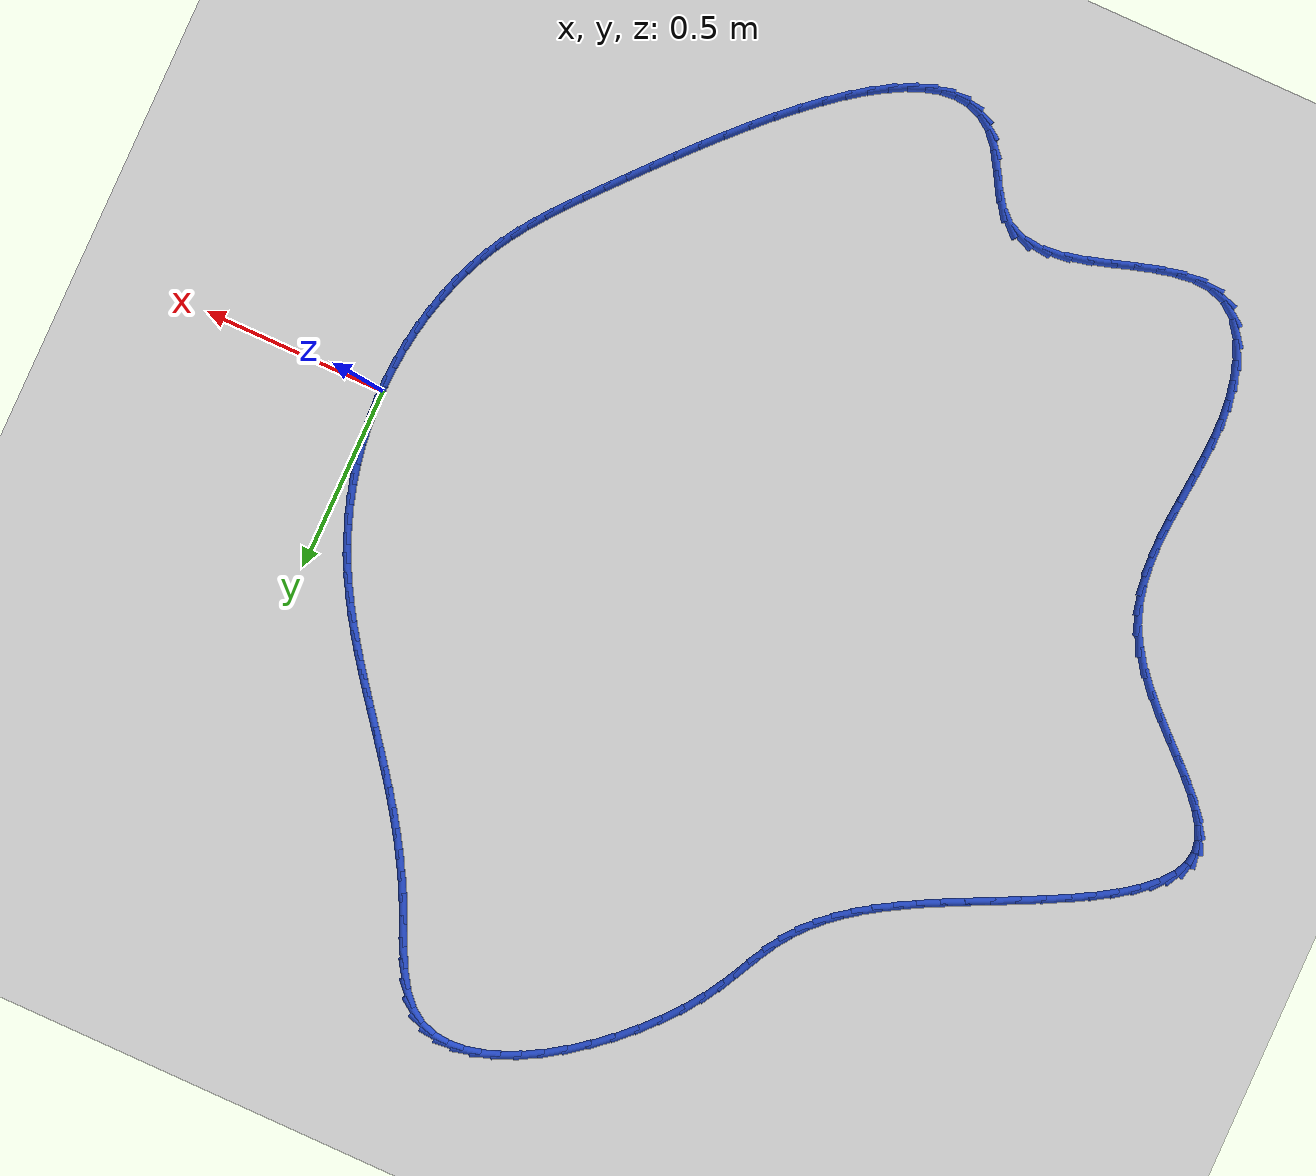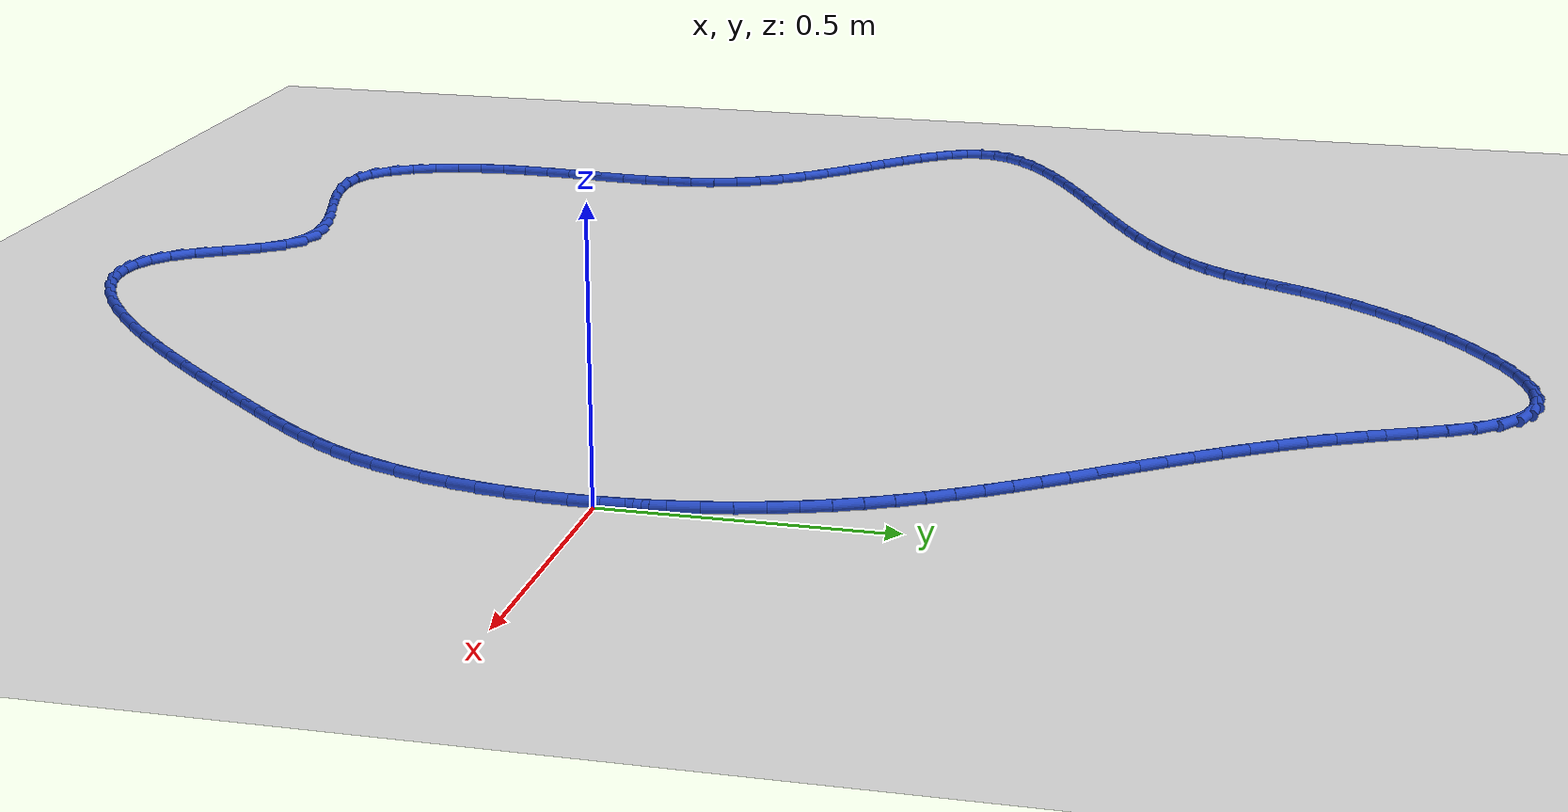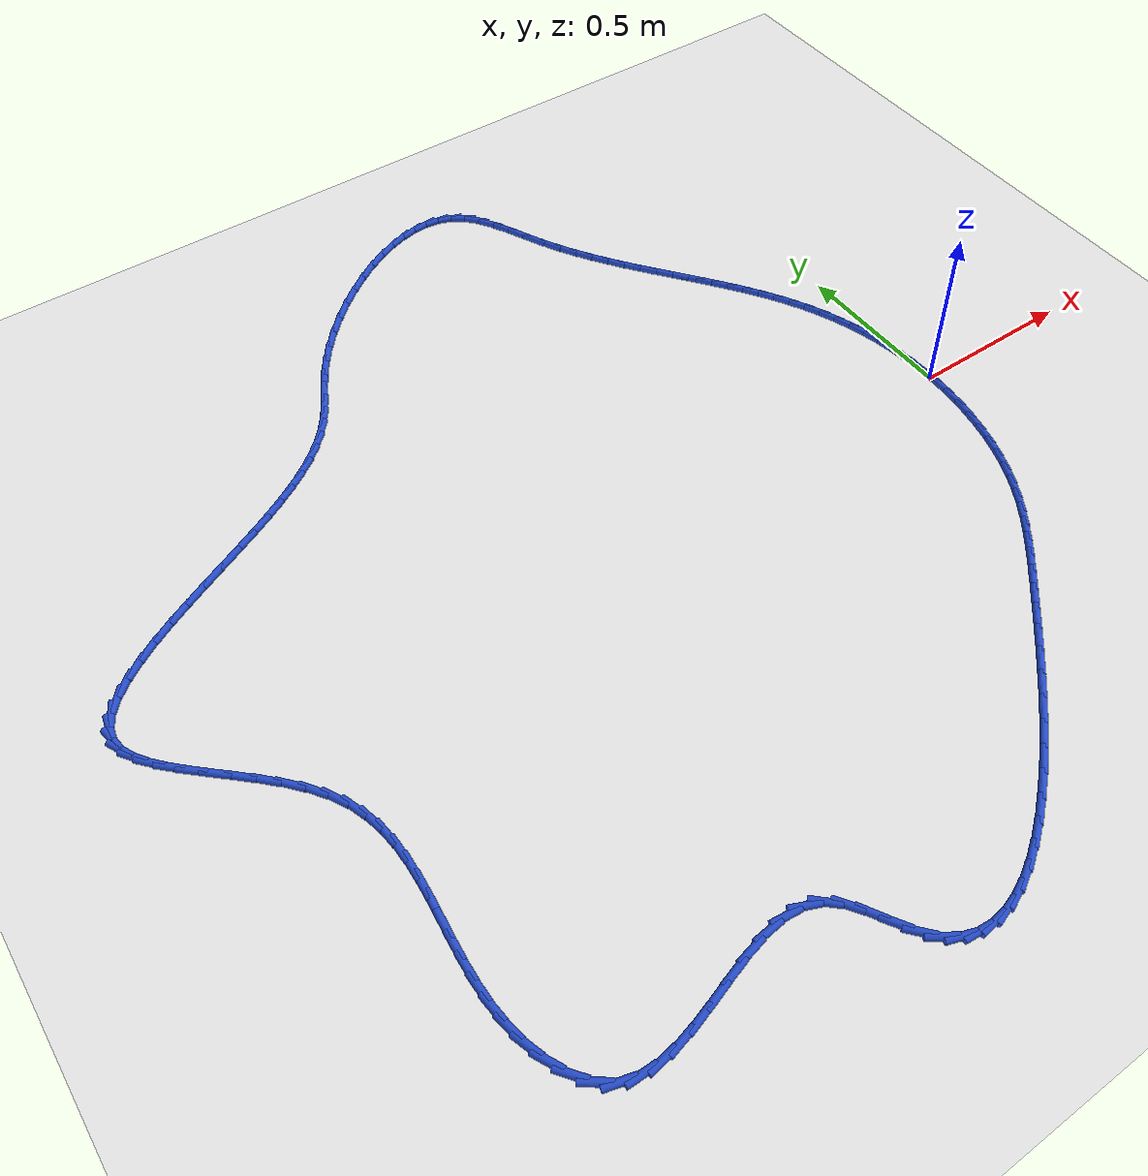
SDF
<sdf version="1.6">
 <world name="default">
  <light name="sun" type="directional">
   <pose>0 0 10 0 -0 0</pose>
   <diffuse>0.8 0.8 0.8 1</diffuse>
   <specular>0.2 0.2 0.2 1</specular>
   <attenuation>
    <range>1000</range>
    <constant>0.9</constant>
    <linear>0.01</linear>
    <quadratic>0.001</quadratic>
   </attenuation>
   <direction>-0.5 0.1 -0.9</direction>
  </light>
  <model name="ground_plane">
   <static>1</static>
   <link name="link">
    <collision name="collision">
     <geometry><plane><normal>0 0 1</normal><size>100 100</size></plane></geometry>
     <surface><friction><ode><mu>100</mu><mu2>50</mu2></ode></friction></surface>
    </collision>
    <visual name="visual">
     <cast_shadows>0</cast_shadows>
     <geometry><plane><normal>0 0 1</normal><size>100 100</size></plane></geometry>
     <material>
      <script><uri>file://media/materials/scripts/gazebo.material</uri><name>Gazebo/WhiteGlow</name></script>
     </material>
    </visual>
   </link>
  </model>
  <gravity>0 0 -9.8</gravity>
  <magnetic_field>6e-06 2.3e-05 -4.2e-05</magnetic_field>
  <atmosphere type="adiabatic"/>
  <physics name="default_physics" default="0" type="ode">
   <max_step_size>0.001</max_step_size>
   <real_time_factor>1</real_time_factor>
   <real_time_update_rate>1000</real_time_update_rate>
  </physics>
  <scene><ambient>0.4 0.4 0.4 1</ambient><background>0.7 0.7 0.7 1</background><shadows>1</shadows></scene>
  <spherical_coordinates>
   <surface_model>EARTH_WGS84</surface_model>
   <latitude_deg>0</latitude_deg>
   <longitude_deg>0</longitude_deg>
   <elevation>0</elevation>
   <heading_deg>0</heading_deg>
  </spherical_coordinates>
  <model name="line">
   <link name="link_0">
    <pose>-1.0408340855860843e-17 9.71445146547012e-17 0.01 0 1.57 -1.5418892007476261</pose>
    <collision name="collision">
     <geometry><cylinder><radius>0.01</radius><length>0.08</length></cylinder></geometry>
    </collision>
    <visual name="visual">
     <material>
      <script><name>Gazebo/Blue</name><uri>file://media/materials/scripts/gazebo.material</uri></script>
     </material>
     <geometry><cylinder><radius>0.01</radius><length>0.08</length></cylinder></geometry>
    </visual>
   </link>
   <link name="link_1">
    <pose>-0.0015468377325302059 0.05349569683326053 0.01 0 1.57 -1.488320773407916</pose>
    <collision name="collision">
     <geometry><cylinder><radius>0.01</radius><length>0.08</length></cylinder></geometry>
    </collision>
    <visual name="visual">
     <material>
      <script><name>Gazebo/Blue</name><uri>file://media/materials/scripts/gazebo.material</uri></script>
     </material>
     <geometry><cylinder><radius>0.01</radius><length>0.08</length></cylinder></geometry>
    </visual>
   </link>
   <link name="link_2">
    <pose>-0.005937765961215691 0.1066140757415775 0.01 0 1.57 -1.435700737468811</pose>
    <collision name="collision">
     <geometry><cylinder><radius>0.01</radius><length>0.08</length></cylinder></geometry>
    </collision>
    <visual name="visual">
     <material>
      <script><name>Gazebo/Blue</name><uri>file://media/materials/scripts/gazebo.material</uri></script>
     </material>
     <geometry><cylinder><radius>0.01</radius><length>0.08</length></cylinder></geometry>
    </visual>
   </link>
   <link name="link_3">
    <pose>-0.013083740268007614 0.15918757619750498 0.01 0 1.57 -1.3838091675171387</pose>
    <collision name="collision">
     <geometry><cylinder><radius>0.01</radius><length>0.08</length></cylinder></geometry>
    </collision>
    <visual name="visual">
     <material>
      <script><name>Gazebo/Blue</name><uri>file://media/materials/scripts/gazebo.material</uri></script>
     </material>
     <geometry><cylinder><radius>0.01</radius><length>0.08</length></cylinder></geometry>
    </visual>
   </link>
   <link name="link_4">
    <pose>-0.022895716234857172 0.21104863767359694 0.01 0 1.57 -1.3324067605446857</pose>
    <collision name="collision">
     <geometry><cylinder><radius>0.01</radius><length>0.08</length></cylinder></geometry>
    </collision>
    <visual name="visual">
     <material>
      <script><name>Gazebo/Blue</name><uri>file://media/materials/scripts/gazebo.material</uri></script>
     </material>
     <geometry><cylinder><radius>0.01</radius><length>0.08</length></cylinder></geometry>
    </visual>
   </link>
   <link name="link_5">
    <pose>-0.035284649443715496 0.26202969964240724 0.01 0 1.57 -1.28123679257852</pose>
    <collision name="collision">
     <geometry><cylinder><radius>0.01</radius><length>0.08</length></cylinder></geometry>
    </collision>
    <visual name="visual">
     <material>
      <script><name>Gazebo/Blue</name><uri>file://media/materials/scripts/gazebo.material</uri></script>
     </material>
     <geometry><cylinder><radius>0.01</radius><length>0.08</length></cylinder></geometry>
    </visual>
   </link>
   <link name="link_6">
    <pose>-0.0501614954765338 0.31196320157648993 0.01 0 1.57 -1.2300261875815097</pose>
    <collision name="collision">
     <geometry><cylinder><radius>0.01</radius><length>0.08</length></cylinder></geometry>
    </collision>
    <visual name="visual">
     <material>
      <script><name>Gazebo/Blue</name><uri>file://media/materials/scripts/gazebo.material</uri></script>
     </material>
     <geometry><cylinder><radius>0.01</radius><length>0.08</length></cylinder></geometry>
    </visual>
   </link>
   <link name="link_7">
    <pose>-0.0674372099152632 0.36068158294839886 0.01 0 1.57 -1.1784859244006887</pose>
    <collision name="collision">
     <geometry><cylinder><radius>0.01</radius><length>0.08</length></cylinder></geometry>
    </collision>
    <visual name="visual">
     <material>
      <script><name>Gazebo/Blue</name><uri>file://media/materials/scripts/gazebo.material</uri></script>
     </material>
     <geometry><cylinder><radius>0.01</radius><length>0.08</length></cylinder></geometry>
    </visual>
   </link>
   <link name="link_8">
    <pose>-0.0870227478804155 0.40801728451120045 0.01 0 1.57 -1.127307303523416</pose>
    <collision name="collision">
     <geometry><cylinder><radius>0.01</radius><length>0.08</length></cylinder></geometry>
    </collision>
    <visual name="visual">
     <material>
      <script><name>Gazebo/Blue</name><uri>file://media/materials/scripts/gazebo.material</uri></script>
     </material>
     <geometry><cylinder><radius>0.01</radius><length>0.08</length></cylinder></geometry>
    </visual>
   </link>
   <link name="link_9">
    <pose>-0.10880493511613067 0.45386970698889045 0.01 0 1.57 -1.0802213030149441</pose>
    <collision name="collision">
     <geometry><cylinder><radius>0.01</radius><length>0.08</length></cylinder></geometry>
    </collision>
    <visual name="visual">
     <material>
      <script><name>Gazebo/Blue</name><uri>file://media/materials/scripts/gazebo.material</uri></script>
     </material>
     <geometry><cylinder><radius>0.01</radius><length>0.08</length></cylinder></geometry>
    </visual>
   </link>
   <link name="link_10">
    <pose>-0.13258171016623557 0.4983849165914367 0.01 0 1.57 -1.0385467871221203</pose>
    <collision name="collision">
     <geometry><cylinder><radius>0.01</radius><length>0.08</length></cylinder></geometry>
    </collision>
    <visual name="visual">
     <material>
      <script><name>Gazebo/Blue</name><uri>file://media/materials/scripts/gazebo.material</uri></script>
     </material>
     <geometry><cylinder><radius>0.01</radius><length>0.08</length></cylinder></geometry>
    </visual>
   </link>
   <link name="link_11">
    <pose>-0.15813054873904492 0.5417657647042686 0.01 0 1.57 -1.002640450113896</pose>
    <collision name="collision">
     <geometry><cylinder><radius>0.01</radius><length>0.08</length></cylinder></geometry>
    </collision>
    <visual name="visual">
     <material>
      <script><name>Gazebo/Blue</name><uri>file://media/materials/scripts/gazebo.material</uri></script>
     </material>
     <geometry><cylinder><radius>0.01</radius><length>0.08</length></cylinder></geometry>
    </visual>
   </link>
   <link name="link_12">
    <pose>-0.1852289265428732 0.5842151027128144 0.01 0 1.57 -0.9727133483149497</pose>
    <collision name="collision">
     <geometry><cylinder><radius>0.01</radius><length>0.08</length></cylinder></geometry>
    </collision>
    <visual name="visual">
     <material>
      <script><name>Gazebo/Blue</name><uri>file://media/materials/scripts/gazebo.material</uri></script>
     </material>
     <geometry><cylinder><radius>0.01</radius><length>0.08</length></cylinder></geometry>
    </visual>
   </link>
   <link name="link_13">
    <pose>-0.21365431928603498 0.6259357820025035 0.01 0 1.57 -0.9488615186285746</pose>
    <collision name="collision">
     <geometry><cylinder><radius>0.01</radius><length>0.08</length></cylinder></geometry>
    </collision>
    <visual name="visual">
     <material>
      <script><name>Gazebo/Blue</name><uri>file://media/materials/scripts/gazebo.material</uri></script>
     </material>
     <geometry><cylinder><radius>0.01</radius><length>0.08</length></cylinder></geometry>
    </visual>
   </link>
   <link name="link_14">
    <pose>-0.24318420267684482 0.6671306539587646 0.01 0 1.57 -0.9310967732679925</pose>
    <collision name="collision">
     <geometry><cylinder><radius>0.01</radius><length>0.08</length></cylinder></geometry>
    </collision>
    <visual name="visual">
     <material>
      <script><name>Gazebo/Blue</name><uri>file://media/materials/scripts/gazebo.material</uri></script>
     </material>
     <geometry><cylinder><radius>0.01</radius><length>0.08</length></cylinder></geometry>
    </visual>
   </link>
   <link name="link_15">
    <pose>-0.27359605242361734 0.7080025699670266 0.01 0 1.57 -0.9193735820314799</pose>
    <collision name="collision">
     <geometry><cylinder><radius>0.01</radius><length>0.08</length></cylinder></geometry>
    </collision>
    <visual name="visual">
     <material>
      <script><name>Gazebo/Blue</name><uri>file://media/materials/scripts/gazebo.material</uri></script>
     </material>
     <geometry><cylinder><radius>0.01</radius><length>0.08</length></cylinder></geometry>
    </visual>
   </link>
   <link name="link_16">
    <pose>-0.304667344234667 0.7487543814127184 0.01 0 1.57 -0.9136098692198911</pose>
    <collision name="collision">
     <geometry><cylinder><radius>0.01</radius><length>0.08</length></cylinder></geometry>
    </collision>
    <visual name="visual">
     <material>
      <script><name>Gazebo/Blue</name><uri>file://media/materials/scripts/gazebo.material</uri></script>
     </material>
     <geometry><cylinder><radius>0.01</radius><length>0.08</length></cylinder></geometry>
    </visual>
   </link>
   <link name="link_17">
    <pose>-0.33617555381830866 0.7895889396812692 0.01 0 1.57 -0.9137009693980482</pose>
    <collision name="collision">
     <geometry><cylinder><radius>0.01</radius><length>0.08</length></cylinder></geometry>
    </collision>
    <visual name="visual">
     <material>
      <script><name>Gazebo/Blue</name><uri>file://media/materials/scripts/gazebo.material</uri></script>
     </material>
     <geometry><cylinder><radius>0.01</radius><length>0.08</length></cylinder></geometry>
    </visual>
   </link>
   <link name="link_18">
    <pose>-0.36789815688285665 0.8307090961581076 0.01 0 1.57 -0.9195268614832072</pose>
    <collision name="collision">
     <geometry><cylinder><radius>0.01</radius><length>0.08</length></cylinder></geometry>
    </collision>
    <visual name="visual">
     <material>
      <script><name>Gazebo/Blue</name><uri>file://media/materials/scripts/gazebo.material</uri></script>
     </material>
     <geometry><cylinder><radius>0.01</radius><length>0.08</length></cylinder></geometry>
    </visual>
   </link>
   <link name="link_19">
    <pose>-0.39961262913662554 0.8723177022286628 0.01 0 1.57 -0.9309532657640962</pose>
    <collision name="collision">
     <geometry><cylinder><radius>0.01</radius><length>0.08</length></cylinder></geometry>
    </collision>
    <visual name="visual">
     <material>
      <script><name>Gazebo/Blue</name><uri>file://media/materials/scripts/gazebo.material</uri></script>
     </material>
     <geometry><cylinder><radius>0.01</radius><length>0.08</length></cylinder></geometry>
    </visual>
   </link>
   <link name="link_20">
    <pose>-0.43109644628793 0.9146176092783636 0.01 0 1.57 -0.9478274252846886</pose>
    <collision name="collision">
     <geometry><cylinder><radius>0.01</radius><length>0.08</length></cylinder></geometry>
    </collision>
    <visual name="visual">
     <material>
      <script><name>Gazebo/Blue</name><uri>file://media/materials/scripts/gazebo.material</uri></script>
     </material>
     <geometry><cylinder><radius>0.01</radius><length>0.08</length></cylinder></geometry>
    </visual>
   </link>
   <link name="link_21">
    <pose>-0.46212708404508474 0.9578116686926388 0.01 0 1.57 -0.9699695649003346</pose>
    <collision name="collision">
     <geometry><cylinder><radius>0.01</radius><length>0.08</length></cylinder></geometry>
    </collision>
    <visual name="visual">
     <material>
      <script><name>Gazebo/Blue</name><uri>file://media/materials/scripts/gazebo.material</uri></script>
     </material>
     <geometry><cylinder><radius>0.01</radius><length>0.08</length></cylinder></geometry>
    </visual>
   </link>
   <link name="link_22">
    <pose>-0.49248201811640385 1.0021027318569173 0.01 0 1.57 -0.9971612428680933</pose>
    <collision name="collision">
     <geometry><cylinder><radius>0.01</radius><length>0.08</length></cylinder></geometry>
    </collision>
    <visual name="visual">
     <material>
      <script><name>Gazebo/Blue</name><uri>file://media/materials/scripts/gazebo.material</uri></script>
     </material>
     <geometry><cylinder><radius>0.01</radius><length>0.08</length></cylinder></geometry>
    </visual>
   </link>
   <link name="link_23">
    <pose>-0.5219387242102026 1.0476936501566283 0.01 0 1.57 -1.0291321327775087</pose>
    <collision name="collision">
     <geometry><cylinder><radius>0.01</radius><length>0.08</length></cylinder></geometry>
    </collision>
    <visual name="visual">
     <material>
      <script><name>Gazebo/Blue</name><uri>file://media/materials/scripts/gazebo.material</uri></script>
     </material>
     <geometry><cylinder><radius>0.01</radius><length>0.08</length></cylinder></geometry>
    </visual>
   </link>
   <link name="link_24">
    <pose>-0.5502746780347949 1.0947872749772003 0.01 0 1.57 -1.0655471751802412</pose>
    <collision name="collision">
     <geometry><cylinder><radius>0.01</radius><length>0.08</length></cylinder></geometry>
    </collision>
    <visual name="visual">
     <material>
      <script><name>Gazebo/Blue</name><uri>file://media/materials/scripts/gazebo.material</uri></script>
     </material>
     <geometry><cylinder><radius>0.01</radius><length>0.08</length></cylinder></geometry>
    </visual>
   </link>
   <link name="link_25">
    <pose>-0.5772673552984958 1.1435864577040629 0.01 0 1.57 -1.1057685655062883</pose>
    <collision name="collision">
     <geometry><cylinder><radius>0.01</radius><length>0.08</length></cylinder></geometry>
    </collision>
    <visual name="visual">
     <material>
      <script><name>Gazebo/Blue</name><uri>file://media/materials/scripts/gazebo.material</uri></script>
     </material>
     <geometry><cylinder><radius>0.01</radius><length>0.08</length></cylinder></geometry>
    </visual>
   </link>
   <link name="link_26">
    <pose>-0.6027019691381644 1.1942806502202241 0.01 0 1.57 -1.1346516488494216</pose>
    <collision name="collision">
     <geometry><cylinder><radius>0.01</radius><length>0.08</length></cylinder></geometry>
    </collision>
    <visual name="visual">
     <material>
      <script><name>Gazebo/Blue</name><uri>file://media/materials/scripts/gazebo.material</uri></script>
     </material>
     <geometry><cylinder><radius>0.01</radius><length>0.08</length></cylinder></geometry>
    </visual>
   </link>
   <link name="link_27">
    <pose>-0.6268823803003694 1.2461611222980022 0.01 0 1.57 -1.1291887097593125</pose>
    <collision name="collision">
     <geometry><cylinder><radius>0.01</radius><length>0.08</length></cylinder></geometry>
    </collision>
    <visual name="visual">
     <material>
      <script><name>Gazebo/Blue</name><uri>file://media/materials/scripts/gazebo.material</uri></script>
     </material>
     <geometry><cylinder><radius>0.01</radius><length>0.08</length></cylinder></geometry>
    </visual>
   </link>
   <link name="link_28">
    <pose>-0.6509493002888308 1.297069904640025 0.01 0 1.57 -1.0847999282130536</pose>
    <collision name="collision">
     <geometry><cylinder><radius>0.01</radius><length>0.08</length></cylinder></geometry>
    </collision>
    <visual name="visual">
     <material>
      <script><name>Gazebo/Blue</name><uri>file://media/materials/scripts/gazebo.material</uri></script>
     </material>
     <geometry><cylinder><radius>0.01</radius><length>0.08</length></cylinder></geometry>
    </visual>
   </link>
   <link name="link_29">
    <pose>-0.6761194211626106 1.3447174465547518 0.01 0 1.57 -0.9923011185499729</pose>
    <collision name="collision">
     <geometry><cylinder><radius>0.01</radius><length>0.08</length></cylinder></geometry>
    </collision>
    <visual name="visual">
     <material>
      <script><name>Gazebo/Blue</name><uri>file://media/materials/scripts/gazebo.material</uri></script>
     </material>
     <geometry><cylinder><radius>0.01</radius><length>0.08</length></cylinder></geometry>
    </visual>
   </link>
   <link name="link_30">
    <pose>-0.7036094349807707 1.3868141973506423 0.01 0 1.57 -0.8348318362751951</pose>
    <collision name="collision">
     <geometry><cylinder><radius>0.01</radius><length>0.08</length></cylinder></geometry>
    </collision>
    <visual name="visual">
     <material>
      <script><name>Gazebo/Blue</name><uri>file://media/materials/scripts/gazebo.material</uri></script>
     </material>
     <geometry><cylinder><radius>0.01</radius><length>0.08</length></cylinder></geometry>
    </visual>
   </link>
   <link name="link_31">
    <pose>-0.7346360338023729 1.4210706063361556 0.01 0 1.57 -0.5983383203894156</pose>
    <collision name="collision">
     <geometry><cylinder><radius>0.01</radius><length>0.08</length></cylinder></geometry>
    </collision>
    <visual name="visual">
     <material>
      <script><name>Gazebo/Blue</name><uri>file://media/materials/scripts/gazebo.material</uri></script>
     </material>
     <geometry><cylinder><radius>0.01</radius><length>0.08</length></cylinder></geometry>
    </visual>
   </link>
   <link name="link_32">
    <pose>-0.7702984508221887 1.4453816816787068 0.01 0 1.57 -0.3367074194109412</pose>
    <collision name="collision">
     <geometry><cylinder><radius>0.01</radius><length>0.08</length></cylinder></geometry>
    </collision>
    <visual name="visual">
     <material>
      <script><name>Gazebo/Blue</name><uri>file://media/materials/scripts/gazebo.material</uri></script>
     </material>
     <geometry><cylinder><radius>0.01</radius><length>0.08</length></cylinder></geometry>
    </visual>
   </link>
   <link name="link_33">
    <pose>-0.8105353099904434 1.4594660548129965 0.01 0 1.57 -0.10432110111384105</pose>
    <collision name="collision">
     <geometry><cylinder><radius>0.01</radius><length>0.08</length></cylinder></geometry>
    </collision>
    <visual name="visual">
     <material>
      <script><name>Gazebo/Blue</name><uri>file://media/materials/scripts/gazebo.material</uri></script>
     </material>
     <geometry><cylinder><radius>0.01</radius><length>0.08</length></cylinder></geometry>
    </visual>
   </link>
   <link name="link_34">
    <pose>-0.854623486190706 1.4640821395128059 0.01 0 1.57 0.08624600560046985</pose>
    <collision name="collision">
     <geometry><cylinder><radius>0.01</radius><length>0.08</length></cylinder></geometry>
    </collision>
    <visual name="visual">
     <material>
      <script><name>Gazebo/Blue</name><uri>file://media/materials/scripts/gazebo.material</uri></script>
     </material>
     <geometry><cylinder><radius>0.01</radius><length>0.08</length></cylinder></geometry>
    </visual>
   </link>
   <link name="link_35">
    <pose>-0.9018321497345708 1.4600004554667936 0.01 0 1.57 0.23755212516329294</pose>
    <collision name="collision">
     <geometry><cylinder><radius>0.01</radius><length>0.08</length></cylinder></geometry>
    </collision>
    <visual name="visual">
     <material>
      <script><name>Gazebo/Blue</name><uri>file://media/materials/scripts/gazebo.material</uri></script>
     </material>
     <geometry><cylinder><radius>0.01</radius><length>0.08</length></cylinder></geometry>
    </visual>
   </link>
   <link name="link_36">
    <pose>-0.9514304709336325 1.447991522363616 0.01 0 1.57 0.35781645446618937</pose>
    <collision name="collision">
     <geometry><cylinder><radius>0.01</radius><length>0.08</length></cylinder></geometry>
    </collision>
    <visual name="visual">
     <material>
      <script><name>Gazebo/Blue</name><uri>file://media/materials/scripts/gazebo.material</uri></script>
     </material>
     <geometry><cylinder><radius>0.01</radius><length>0.08</length></cylinder></geometry>
    </visual>
   </link>
   <link name="link_37">
    <pose>-1.0026876200994854 1.428825859891931 0.01 0 1.57 0.4553243321221153</pose>
    <collision name="collision">
     <geometry><cylinder><radius>0.01</radius><length>0.08</length></cylinder></geometry>
    </collision>
    <visual name="visual">
     <material>
      <script><name>Gazebo/Blue</name><uri>file://media/materials/scripts/gazebo.material</uri></script>
     </material>
     <geometry><cylinder><radius>0.01</radius><length>0.08</length></cylinder></geometry>
    </visual>
   </link>
   <link name="link_38">
    <pose>-1.0548727675437244 1.4032739877403957 0.01 0 1.57 0.5367361043253207</pose>
    <collision name="collision">
     <geometry><cylinder><radius>0.01</radius><length>0.08</length></cylinder></geometry>
    </collision>
    <visual name="visual">
     <material>
      <script><name>Gazebo/Blue</name><uri>file://media/materials/scripts/gazebo.material</uri></script>
     </material>
     <geometry><cylinder><radius>0.01</radius><length>0.08</length></cylinder></geometry>
    </visual>
   </link>
   <link name="link_39">
    <pose>-1.1072550835779433 1.372106425597668 0.01 0 1.57 0.6070751255620307</pose>
    <collision name="collision">
     <geometry><cylinder><radius>0.01</radius><length>0.08</length></cylinder></geometry>
    </collision>
    <visual name="visual">
     <material>
      <script><name>Gazebo/Blue</name><uri>file://media/materials/scripts/gazebo.material</uri></script>
     </material>
     <geometry><cylinder><radius>0.01</radius><length>0.08</length></cylinder></geometry>
    </visual>
   </link>
   <link name="link_40">
    <pose>-1.1591037385137368 1.3360936931524052 0.01 0 1.57 0.6701441258648317</pose>
    <collision name="collision">
     <geometry><cylinder><radius>0.01</radius><length>0.08</length></cylinder></geometry>
    </collision>
    <visual name="visual">
     <material>
      <script><name>Gazebo/Blue</name><uri>file://media/materials/scripts/gazebo.material</uri></script>
     </material>
     <geometry><cylinder><radius>0.01</radius><length>0.08</length></cylinder></geometry>
    </visual>
   </link>
   <link name="link_41">
    <pose>-1.2096879026627 1.2960063100932637 0.01 0 1.57 0.7289534064258657</pose>
    <collision name="collision">
     <geometry><cylinder><radius>0.01</radius><length>0.08</length></cylinder></geometry>
    </collision>
    <visual name="visual">
     <material>
      <script><name>Gazebo/Blue</name><uri>file://media/materials/scripts/gazebo.material</uri></script>
     </material>
     <geometry><cylinder><radius>0.01</radius><length>0.08</length></cylinder></geometry>
    </visual>
   </link>
   <link name="link_42">
    <pose>-1.2582767463364266 1.2526147961089023 0.01 0 1.57 0.7860783375433793</pose>
    <collision name="collision">
     <geometry><cylinder><radius>0.01</radius><length>0.08</length></cylinder></geometry>
    </collision>
    <visual name="visual">
     <material>
      <script><name>Gazebo/Blue</name><uri>file://media/materials/scripts/gazebo.material</uri></script>
     </material>
     <geometry><cylinder><radius>0.01</radius><length>0.08</length></cylinder></geometry>
    </visual>
   </link>
   <link name="link_43">
    <pose>-1.3041394398465114 1.2066896708879775 0.01 0 1.57 0.8439643957295785</pose>
    <collision name="collision">
     <geometry><cylinder><radius>0.01</radius><length>0.08</length></cylinder></geometry>
    </collision>
    <visual name="visual">
     <material>
      <script><name>Gazebo/Blue</name><uri>file://media/materials/scripts/gazebo.material</uri></script>
     </material>
     <geometry><cylinder><radius>0.01</radius><length>0.08</length></cylinder></geometry>
    </visual>
   </link>
   <link name="link_44">
    <pose>-1.3465451535045485 1.1590014541191467 0.01 0 1.57 0.9052245902009057</pose>
    <collision name="collision">
     <geometry><cylinder><radius>0.01</radius><length>0.08</length></cylinder></geometry>
    </collision>
    <visual name="visual">
     <material>
      <script><name>Gazebo/Blue</name><uri>file://media/materials/scripts/gazebo.material</uri></script>
     </material>
     <geometry><cylinder><radius>0.01</radius><length>0.08</length></cylinder></geometry>
    </visual>
   </link>
   <link name="link_45">
    <pose>-1.3847630576221333 1.1103206654910676 0.01 0 1.57 0.9729860494426007</pose>
    <collision name="collision">
     <geometry><cylinder><radius>0.01</radius><length>0.08</length></cylinder></geometry>
    </collision>
    <visual name="visual">
     <material>
      <script><name>Gazebo/Blue</name><uri>file://media/materials/scripts/gazebo.material</uri></script>
     </material>
     <geometry><cylinder><radius>0.01</radius><length>0.08</length></cylinder></geometry>
    </visual>
   </link>
   <link name="link_46">
    <pose>-1.4180623225108593 1.061417824692398 0.01 0 1.57 1.0449753213320043</pose>
    <collision name="collision">
     <geometry><cylinder><radius>0.01</radius><length>0.08</length></cylinder></geometry>
    </collision>
    <visual name="visual">
     <material>
      <script><name>Gazebo/Blue</name><uri>file://media/materials/scripts/gazebo.material</uri></script>
     </material>
     <geometry><cylinder><radius>0.01</radius><length>0.08</length></cylinder></geometry>
    </visual>
   </link>
   <link name="link_47">
    <pose>-1.4461297514862614 1.013052144586911 0.01 0 1.57 1.090087595716561</pose>
    <collision name="collision">
     <geometry><cylinder><radius>0.01</radius><length>0.08</length></cylinder></geometry>
    </collision>
    <visual name="visual">
     <material>
      <script><name>Gazebo/Blue</name><uri>file://media/materials/scripts/gazebo.material</uri></script>
     </material>
     <geometry><cylinder><radius>0.01</radius><length>0.08</length></cylinder></geometry>
    </visual>
   </link>
   <link name="link_48">
    <pose>-1.4707059578086061 0.9659272340291873 0.01 0 1.57 1.092093563156112</pose>
    <collision name="collision">
     <geometry><cylinder><radius>0.01</radius><length>0.08</length></cylinder></geometry>
    </collision>
    <visual name="visual">
     <material>
      <script><name>Gazebo/Blue</name><uri>file://media/materials/scripts/gazebo.material</uri></script>
     </material>
     <geometry><cylinder><radius>0.01</radius><length>0.08</length></cylinder></geometry>
    </visual>
   </link>
   <link name="link_49">
    <pose>-1.4941618435281392 0.9207296376932786 0.01 0 1.57 1.0450708413862715</pose>
    <collision name="collision">
     <geometry><cylinder><radius>0.01</radius><length>0.08</length></cylinder></geometry>
    </collision>
    <visual name="visual">
     <material>
      <script><name>Gazebo/Blue</name><uri>file://media/materials/scripts/gazebo.material</uri></script>
     </material>
     <geometry><cylinder><radius>0.01</radius><length>0.08</length></cylinder></geometry>
    </visual>
   </link>
   <link name="link_50">
    <pose>-1.5188684780638124 0.878145895721964 0.01 0 1.57 0.9538484667478597</pose>
    <collision name="collision">
     <geometry><cylinder><radius>0.01</radius><length>0.08</length></cylinder></geometry>
    </collision>
    <visual name="visual">
     <material>
      <script><name>Gazebo/Blue</name><uri>file://media/materials/scripts/gazebo.material</uri></script>
     </material>
     <geometry><cylinder><radius>0.01</radius><length>0.08</length></cylinder></geometry>
    </visual>
   </link>
   <link name="link_51">
    <pose>-1.5468450535640592 0.838704009540155 0.01 0 1.57 0.8568633004463845</pose>
    <collision name="collision">
     <geometry><cylinder><radius>0.01</radius><length>0.08</length></cylinder></geometry>
    </collision>
    <visual name="visual">
     <material>
      <script><name>Gazebo/Blue</name><uri>file://media/materials/scripts/gazebo.material</uri></script>
     </material>
     <geometry><cylinder><radius>0.01</radius><length>0.08</length></cylinder></geometry>
    </visual>
   </link>
   <link name="link_52">
    <pose>-1.5784758116451472 0.8021953516885841 0.01 0 1.57 0.7681025868073775</pose>
    <collision name="collision">
     <geometry><cylinder><radius>0.01</radius><length>0.08</length></cylinder></geometry>
    </collision>
    <visual name="visual">
     <material>
      <script><name>Gazebo/Blue</name><uri>file://media/materials/scripts/gazebo.material</uri></script>
     </material>
     <geometry><cylinder><radius>0.01</radius><length>0.08</length></cylinder></geometry>
    </visual>
   </link>
   <link name="link_53">
    <pose>-1.6136704975366511 0.7681975098031826 0.01 0 1.57 0.6899247803754159</pose>
    <collision name="collision">
     <geometry><cylinder><radius>0.01</radius><length>0.08</length></cylinder></geometry>
    </collision>
    <visual name="visual">
     <material>
      <script><name>Gazebo/Blue</name><uri>file://media/materials/scripts/gazebo.material</uri></script>
     </material>
     <geometry><cylinder><radius>0.01</radius><length>0.08</length></cylinder></geometry>
    </visual>
   </link>
   <link name="link_54">
    <pose>-1.6523388056232042 0.7362880486116322 0.01 0 1.57 0.62349578380004</pose>
    <collision name="collision">
     <geometry><cylinder><radius>0.01</radius><length>0.08</length></cylinder></geometry>
    </collision>
    <visual name="visual">
     <material>
      <script><name>Gazebo/Blue</name><uri>file://media/materials/scripts/gazebo.material</uri></script>
     </material>
     <geometry><cylinder><radius>0.01</radius><length>0.08</length></cylinder></geometry>
    </visual>
   </link>
   <link name="link_55">
    <pose>-1.694390430289438 0.7060445328416161 0.01 0 1.57 0.5689914432230724</pose>
    <collision name="collision">
     <geometry><cylinder><radius>0.01</radius><length>0.08</length></cylinder></geometry>
    </collision>
    <visual name="visual">
     <material>
      <script><name>Gazebo/Blue</name><uri>file://media/materials/scripts/gazebo.material</uri></script>
     </material>
     <geometry><cylinder><radius>0.01</radius><length>0.08</length></cylinder></geometry>
    </visual>
   </link>
   <link name="link_56">
    <pose>-1.7397350659199842 0.6770445272208157 0.01 0 1.57 0.5259147013051572</pose>
    <collision name="collision">
     <geometry><cylinder><radius>0.01</radius><length>0.08</length></cylinder></geometry>
    </collision>
    <visual name="visual">
     <material>
      <script><name>Gazebo/Blue</name><uri>file://media/materials/scripts/gazebo.material</uri></script>
     </material>
     <geometry><cylinder><radius>0.01</radius><length>0.08</length></cylinder></geometry>
    </visual>
   </link>
   <link name="link_57">
    <pose>-1.7882824068994763 0.6488655964769138 0.01 0 1.57 0.4933935872202117</pose>
    <collision name="collision">
     <geometry><cylinder><radius>0.01</radius><length>0.08</length></cylinder></geometry>
    </collision>
    <visual name="visual">
     <material>
      <script><name>Gazebo/Blue</name><uri>file://media/materials/scripts/gazebo.material</uri></script>
     </material>
     <geometry><cylinder><radius>0.01</radius><length>0.08</length></cylinder></geometry>
    </visual>
   </link>
   <link name="link_58">
    <pose>-1.8399421476125468 0.6210853053375922 0.01 0 1.57 0.4704093641441977</pose>
    <collision name="collision">
     <geometry><cylinder><radius>0.01</radius><length>0.08</length></cylinder></geometry>
    </collision>
    <visual name="visual">
     <material>
      <script><name>Gazebo/Blue</name><uri>file://media/materials/scripts/gazebo.material</uri></script>
     </material>
     <geometry><cylinder><radius>0.01</radius><length>0.08</length></cylinder></geometry>
    </visual>
   </link>
   <link name="link_59">
    <pose>-1.8946203905497763 0.5932824578877812 0.01 0 1.57 0.45666396141137294</pose>
    <collision name="collision">
     <geometry><cylinder><radius>0.01</radius><length>0.08</length></cylinder></geometry>
    </collision>
    <visual name="visual">
     <material>
      <script><name>Gazebo/Blue</name><uri>file://media/materials/scripts/gazebo.material</uri></script>
     </material>
     <geometry><cylinder><radius>0.01</radius><length>0.08</length></cylinder></geometry>
    </visual>
   </link>
   <link name="link_60">
    <pose>-1.9518559533707762 0.5651625872057742 0.01 0 1.57 0.4522741626615246</pose>
    <collision name="collision">
     <geometry><cylinder><radius>0.01</radius><length>0.08</length></cylinder></geometry>
    </collision>
    <visual name="visual">
     <material>
      <script><name>Gazebo/Blue</name><uri>file://media/materials/scripts/gazebo.material</uri></script>
     </material>
     <geometry><cylinder><radius>0.01</radius><length>0.08</length></cylinder></geometry>
    </visual>
   </link>
   <link name="link_61">
    <pose>-2.010507952283484 0.5366657524746595 0.01 0 1.57 0.4565730462190267</pose>
    <collision name="collision">
     <geometry><cylinder><radius>0.01</radius><length>0.08</length></cylinder></geometry>
    </collision>
    <visual name="visual">
     <material>
      <script><name>Gazebo/Blue</name><uri>file://media/materials/scripts/gazebo.material</uri></script>
     </material>
     <geometry><cylinder><radius>0.01</radius><length>0.08</length></cylinder></geometry>
    </visual>
   </link>
   <link name="link_62">
    <pose>-2.06936190631584 0.5077574070559661 0.01 0 1.57 0.4696279134727496</pose>
    <collision name="collision">
     <geometry><cylinder><radius>0.01</radius><length>0.08</length></cylinder></geometry>
    </collision>
    <visual name="visual">
     <material>
      <script><name>Gazebo/Blue</name><uri>file://media/materials/scripts/gazebo.material</uri></script>
     </material>
     <geometry><cylinder><radius>0.01</radius><length>0.08</length></cylinder></geometry>
    </visual>
   </link>
   <link name="link_63">
    <pose>-2.127203334495774 0.47840300431122285 0.01 0 1.57 0.4923897369800903</pose>
    <collision name="collision">
     <geometry><cylinder><radius>0.01</radius><length>0.08</length></cylinder></geometry>
    </collision>
    <visual name="visual">
     <material>
      <script><name>Gazebo/Blue</name><uri>file://media/materials/scripts/gazebo.material</uri></script>
     </material>
     <geometry><cylinder><radius>0.01</radius><length>0.08</length></cylinder></geometry>
    </visual>
   </link>
   <link name="link_64">
    <pose>-2.182817755851227 0.44856799760195876 0.01 0 1.57 0.5268715682375054</pose>
    <collision name="collision">
     <geometry><cylinder><radius>0.01</radius><length>0.08</length></cylinder></geometry>
    </collision>
    <visual name="visual">
     <material>
      <script><name>Gazebo/Blue</name><uri>file://media/materials/scripts/gazebo.material</uri></script>
     </material>
     <geometry><cylinder><radius>0.01</radius><length>0.08</length></cylinder></geometry>
    </visual>
   </link>
   <link name="link_65">
    <pose>-2.2349906894101323 0.41821784028970255 0.01 0 1.57 0.5765797628587735</pose>
    <collision name="collision">
     <geometry><cylinder><radius>0.01</radius><length>0.08</length></cylinder></geometry>
    </collision>
    <visual name="visual">
     <material>
      <script><name>Gazebo/Blue</name><uri>file://media/materials/scripts/gazebo.material</uri></script>
     </material>
     <geometry><cylinder><radius>0.01</radius><length>0.08</length></cylinder></geometry>
    </visual>
   </link>
   <link name="link_66">
    <pose>-2.2825076542004283 0.38731798573598303 0.01 0 1.57 0.6473198722779677</pose>
    <collision name="collision">
     <geometry><cylinder><radius>0.01</radius><length>0.08</length></cylinder></geometry>
    </collision>
    <visual name="visual">
     <material>
      <script><name>Gazebo/Blue</name><uri>file://media/materials/scripts/gazebo.material</uri></script>
     </material>
     <geometry><cylinder><radius>0.01</radius><length>0.08</length></cylinder></geometry>
    </visual>
   </link>
   <link name="link_67">
    <pose>-2.324154169250049 0.355833887302329 0.01 0 1.57 0.7485332283813007</pose>
    <collision name="collision">
     <geometry><cylinder><radius>0.01</radius><length>0.08</length></cylinder></geometry>
    </collision>
    <visual name="visual">
     <material>
      <script><name>Gazebo/Blue</name><uri>file://media/materials/scripts/gazebo.material</uri></script>
     </material>
     <geometry><cylinder><radius>0.01</radius><length>0.08</length></cylinder></geometry>
    </visual>
   </link>
   <link name="link_68">
    <pose>-2.3587157535869316 0.3237309983502697 0.01 0 1.57 0.8949916680700544</pose>
    <collision name="collision">
     <geometry><cylinder><radius>0.01</radius><length>0.08</length></cylinder></geometry>
    </collision>
    <visual name="visual">
     <material>
      <script><name>Gazebo/Blue</name><uri>file://media/materials/scripts/gazebo.material</uri></script>
     </material>
     <geometry><cylinder><radius>0.01</radius><length>0.08</length></cylinder></geometry>
    </visual>
   </link>
   <link name="link_69">
    <pose>-2.384977926239011 0.2909747722413337 0.01 0 1.57 1.1065215983021182</pose>
    <collision name="collision">
     <geometry><cylinder><radius>0.01</radius><length>0.08</length></cylinder></geometry>
    </collision>
    <visual name="visual">
     <material>
      <script><name>Gazebo/Blue</name><uri>file://media/materials/scripts/gazebo.material</uri></script>
     </material>
     <geometry><cylinder><radius>0.01</radius><length>0.08</length></cylinder></geometry>
    </visual>
   </link>
   <link name="link_70">
    <pose>-2.4017262062342244 0.25753066233704996 0.01 0 1.57 1.3963933133466595</pose>
    <collision name="collision">
     <geometry><cylinder><radius>0.01</radius><length>0.08</length></cylinder></geometry>
    </collision>
    <visual name="visual">
     <material>
      <script><name>Gazebo/Blue</name><uri>file://media/materials/scripts/gazebo.material</uri></script>
     </material>
     <geometry><cylinder><radius>0.01</radius><length>0.08</length></cylinder></geometry>
    </visual>
   </link>
   <link name="link_71">
    <pose>-2.4077461126005075 0.22336412199894706 0.01 0 1.57 -1.4081685591763498</pose>
    <collision name="collision">
     <geometry><cylinder><radius>0.01</radius><length>0.08</length></cylinder></geometry>
    </collision>
    <visual name="visual">
     <material>
      <script><name>Gazebo/Blue</name><uri>file://media/materials/scripts/gazebo.material</uri></script>
     </material>
     <geometry><cylinder><radius>0.01</radius><length>0.08</length></cylinder></geometry>
    </visual>
   </link>
   <link name="link_72">
    <pose>-2.402015639382396 0.1884385705458123 0.01 0 1.57 -1.134678397477323</pose>
    <collision name="collision">
     <geometry><cylinder><radius>0.01</radius><length>0.08</length></cylinder></geometry>
    </collision>
    <visual name="visual">
     <material>
      <script><name>Gazebo/Blue</name><uri>file://media/materials/scripts/gazebo.material</uri></script>
     </material>
     <geometry><cylinder><radius>0.01</radius><length>0.08</length></cylinder></geometry>
    </visual>
   </link>
   <link name="link_73">
    <pose>-2.385358827044445 0.15269791859660872 0.01 0 1.57 -0.9583298538635758</pose>
    <collision name="collision">
     <geometry><cylinder><radius>0.01</radius><length>0.08</length></cylinder></geometry>
    </collision>
    <visual name="visual">
     <material>
      <script><name>Gazebo/Blue</name><uri>file://media/materials/scripts/gazebo.material</uri></script>
     </material>
     <geometry><cylinder><radius>0.01</radius><length>0.08</length></cylinder></geometry>
    </visual>
   </link>
   <link name="link_74">
    <pose>-2.35962784050536 0.11607521172858677 0.01 0 1.57 -0.8509642586159476</pose>
    <collision name="collision">
     <geometry><cylinder><radius>0.01</radius><length>0.08</length></cylinder></geometry>
    </collision>
    <visual name="visual">
     <material>
      <script><name>Gazebo/Blue</name><uri>file://media/materials/scripts/gazebo.material</uri></script>
     </material>
     <geometry><cylinder><radius>0.01</radius><length>0.08</length></cylinder></geometry>
    </visual>
   </link>
   <link name="link_75">
    <pose>-2.3266859527557564 0.0785033781308113 0.01 0 1.57 -0.7892811523324769</pose>
    <collision name="collision">
     <geometry><cylinder><radius>0.01</radius><length>0.08</length></cylinder></geometry>
    </collision>
    <visual name="visual">
     <material>
      <script><name>Gazebo/Blue</name><uri>file://media/materials/scripts/gazebo.material</uri></script>
     </material>
     <geometry><cylinder><radius>0.01</radius><length>0.08</length></cylinder></geometry>
    </visual>
   </link>
   <link name="link_76">
    <pose>-2.2883964367862513 0.03991534599234652 0.01 0 1.57 -0.7595881403811231</pose>
    <collision name="collision">
     <geometry><cylinder><radius>0.01</radius><length>0.08</length></cylinder></geometry>
    </collision>
    <visual name="visual">
     <material>
      <script><name>Gazebo/Blue</name><uri>file://media/materials/scripts/gazebo.material</uri></script>
     </material>
     <geometry><cylinder><radius>0.01</radius><length>0.08</length></cylinder></geometry>
    </visual>
   </link>
   <link name="link_77">
    <pose>-2.246622565587458 0.0002440435022573982 0.01 0 1.57 -0.7548518289816915</pose>
    <collision name="collision">
     <geometry><cylinder><radius>0.01</radius><length>0.08</length></cylinder></geometry>
    </collision>
    <visual name="visual">
     <material>
      <script><name>Gazebo/Blue</name><uri>file://media/materials/scripts/gazebo.material</uri></script>
     </material>
     <geometry><cylinder><radius>0.01</radius><length>0.08</length></cylinder></geometry>
    </visual>
   </link>
   <link name="link_78">
    <pose>-2.203227612149994 -0.040577601150390816 0.01 0 1.57 -0.7723260092343607</pose>
    <collision name="collision">
     <geometry><cylinder><radius>0.01</radius><length>0.08</length></cylinder></geometry>
    </collision>
    <visual name="visual">
     <material>
      <script><name>Gazebo/Blue</name><uri>file://media/materials/scripts/gazebo.material</uri></script>
     </material>
     <geometry><cylinder><radius>0.01</radius><length>0.08</length></cylinder></geometry>
    </visual>
   </link>
   <link name="link_79">
    <pose>-2.160074849464473 -0.08261665977653479 0.01 0 1.57 -0.8123706736685655</pose>
    <collision name="collision">
     <geometry><cylinder><radius>0.01</radius><length>0.08</length></cylinder></geometry>
    </collision>
    <visual name="visual">
     <material>
      <script><name>Gazebo/Blue</name><uri>file://media/materials/scripts/gazebo.material</uri></script>
     </material>
     <geometry><cylinder><radius>0.01</radius><length>0.08</length></cylinder></geometry>
    </visual>
   </link>
   <link name="link_80">
    <pose>-2.119027550521511 -0.1259402041871085 0.01 0 1.57 -0.8780519830862138</pose>
    <collision name="collision">
     <geometry><cylinder><radius>0.01</radius><length>0.08</length></cylinder></geometry>
    </collision>
    <visual name="visual">
     <material>
      <script><name>Gazebo/Blue</name><uri>file://media/materials/scripts/gazebo.material</uri></script>
     </material>
     <geometry><cylinder><radius>0.01</radius><length>0.08</length></cylinder></geometry>
    </visual>
   </link>
   <link name="link_81">
    <pose>-2.081948988311724 -0.1706153061930488 0.01 0 1.57 -0.9750628348001981</pose>
    <collision name="collision">
     <geometry><cylinder><radius>0.01</radius><length>0.08</length></cylinder></geometry>
    </collision>
    <visual name="visual">
     <material>
      <script><name>Gazebo/Blue</name><uri>file://media/materials/scripts/gazebo.material</uri></script>
     </material>
     <geometry><cylinder><radius>0.01</radius><length>0.08</length></cylinder></geometry>
    </visual>
   </link>
   <link name="link_82">
    <pose>-2.0507024358257273 -0.21670903760529037 0.01 0 1.57 -1.1063157815308573</pose>
    <collision name="collision">
     <geometry><cylinder><radius>0.01</radius><length>0.08</length></cylinder></geometry>
    </collision>
    <visual name="visual">
     <material>
      <script><name>Gazebo/Blue</name><uri>file://media/materials/scripts/gazebo.material</uri></script>
     </material>
     <geometry><cylinder><radius>0.01</radius><length>0.08</length></cylinder></geometry>
    </visual>
   </link>
   <link name="link_83">
    <pose>-2.0268745235784493 -0.264265791455061 0.01 0 1.57 -1.2422747602545667</pose>
    <collision name="collision">
     <geometry><cylinder><radius>0.01</radius><length>0.08</length></cylinder></geometry>
    </collision>
    <visual name="visual">
     <material>
      <script><name>Gazebo/Blue</name><uri>file://media/materials/scripts/gazebo.material</uri></script>
     </material>
     <geometry><cylinder><radius>0.01</radius><length>0.08</length></cylinder></geometry>
    </visual>
   </link>
   <link name="link_84">
    <pose>-2.010201539706212 -0.3131782721831754 0.01 0 1.57 -1.363421133748681</pose>
    <collision name="collision">
     <geometry><cylinder><radius>0.01</radius><length>0.08</length></cylinder></geometry>
    </collision>
    <visual name="visual">
     <material>
      <script><name>Gazebo/Blue</name><uri>file://media/materials/scripts/gazebo.material</uri></script>
     </material>
     <geometry><cylinder><radius>0.01</radius><length>0.08</length></cylinder></geometry>
    </visual>
   </link>
   <link name="link_85">
    <pose>-1.9996607791071037 -0.3632769629811375 0.01 0 1.57 -1.4648939368300327</pose>
    <collision name="collision">
     <geometry><cylinder><radius>0.01</radius><length>0.08</length></cylinder></geometry>
    </collision>
    <visual name="visual">
     <material>
      <script><name>Gazebo/Blue</name><uri>file://media/materials/scripts/gazebo.material</uri></script>
     </material>
     <geometry><cylinder><radius>0.01</radius><length>0.08</length></cylinder></geometry>
    </visual>
   </link>
   <link name="link_86">
    <pose>-1.9942272296047265 -0.41439215790957756 0.01 0 1.57 -1.5447956680932138</pose>
    <collision name="collision">
     <geometry><cylinder><radius>0.01</radius><length>0.08</length></cylinder></geometry>
    </collision>
    <visual name="visual">
     <material>
      <script><name>Gazebo/Blue</name><uri>file://media/materials/scripts/gazebo.material</uri></script>
     </material>
     <geometry><cylinder><radius>0.01</radius><length>0.08</length></cylinder></geometry>
    </visual>
   </link>
   <link name="link_87">
    <pose>-1.9928758790226804 -0.46635415102912336 0.01 0 1.57 1.538401398410963</pose>
    <collision name="collision">
     <geometry><cylinder><radius>0.01</radius><length>0.08</length></cylinder></geometry>
    </collision>
    <visual name="visual">
     <material>
      <script><name>Gazebo/Blue</name><uri>file://media/materials/scripts/gazebo.material</uri></script>
     </material>
     <geometry><cylinder><radius>0.01</radius><length>0.08</length></cylinder></geometry>
    </visual>
   </link>
   <link name="link_88">
    <pose>-1.994581715184566 -0.5189932364004026 0.01 0 1.57 1.5005778343934313</pose>
    <collision name="collision">
     <geometry><cylinder><radius>0.01</radius><length>0.08</length></cylinder></geometry>
    </collision>
    <visual name="visual">
     <material>
      <script><name>Gazebo/Blue</name><uri>file://media/materials/scripts/gazebo.material</uri></script>
     </material>
     <geometry><cylinder><radius>0.01</radius><length>0.08</length></cylinder></geometry>
    </visual>
   </link>
   <link name="link_89">
    <pose>-1.998319725913983 -0.5721397080840454 0.01 0 1.57 1.4823069150414498</pose>
    <collision name="collision">
     <geometry><cylinder><radius>0.01</radius><length>0.08</length></cylinder></geometry>
    </collision>
    <visual name="visual">
     <material>
      <script><name>Gazebo/Blue</name><uri>file://media/materials/scripts/gazebo.material</uri></script>
     </material>
     <geometry><cylinder><radius>0.01</radius><length>0.08</length></cylinder></geometry>
    </visual>
   </link>
   <link name="link_90">
    <pose>-2.0030648990345328 -0.6256238601406796 0.01 0 1.57 1.482912643283614</pose>
    <collision name="collision">
     <geometry><cylinder><radius>0.01</radius><length>0.08</length></cylinder></geometry>
    </collision>
    <visual name="visual">
     <material>
      <script><name>Gazebo/Blue</name><uri>file://media/materials/scripts/gazebo.material</uri></script>
     </material>
     <geometry><cylinder><radius>0.01</radius><length>0.08</length></cylinder></geometry>
    </visual>
   </link>
   <link name="link_91">
    <pose>-2.0077922223698152 -0.6792759866309327 0.01 0 1.57 1.5022286049897857</pose>
    <collision name="collision">
     <geometry><cylinder><radius>0.01</radius><length>0.08</length></cylinder></geometry>
    </collision>
    <visual name="visual">
     <material>
      <script><name>Gazebo/Blue</name><uri>file://media/materials/scripts/gazebo.material</uri></script>
     </material>
     <geometry><cylinder><radius>0.01</radius><length>0.08</length></cylinder></geometry>
    </visual>
   </link>
   <link name="link_92">
    <pose>-2.0114766837434304 -0.7329263816154352 0.01 0 1.57 1.5405770557310856</pose>
    <collision name="collision">
     <geometry><cylinder><radius>0.01</radius><length>0.08</length></cylinder></geometry>
    </collision>
    <visual name="visual">
     <material>
      <script><name>Gazebo/Blue</name><uri>file://media/materials/scripts/gazebo.material</uri></script>
     </material>
     <geometry><cylinder><radius>0.01</radius><length>0.08</length></cylinder></geometry>
    </visual>
   </link>
   <link name="link_93">
    <pose>-2.0130932709789793 -0.7864053391548136 0.01 0 1.57 -1.5430210137961946</pose>
    <collision name="collision">
     <geometry><cylinder><radius>0.01</radius><length>0.08</length></cylinder></geometry>
    </collision>
    <visual name="visual">
     <material>
      <script><name>Gazebo/Blue</name><uri>file://media/materials/scripts/gazebo.material</uri></script>
     </material>
     <geometry><cylinder><radius>0.01</radius><length>0.08</length></cylinder></geometry>
    </visual>
   </link>
   <link name="link_94">
    <pose>-2.011616971900062 -0.8395431533096984 0.01 0 1.57 -1.4648949364211263</pose>
    <collision name="collision">
     <geometry><cylinder><radius>0.01</radius><length>0.08</length></cylinder></geometry>
    </collision>
    <visual name="visual">
     <material>
      <script><name>Gazebo/Blue</name><uri>file://media/materials/scripts/gazebo.material</uri></script>
     </material>
     <geometry><cylinder><radius>0.01</radius><length>0.08</length></cylinder></geometry>
    </visual>
   </link>
   <link name="link_95">
    <pose>-2.0060227743302783 -0.8921701181407171 0.01 0 1.57 -1.3669708003092622</pose>
    <collision name="collision">
     <geometry><cylinder><radius>0.01</radius><length>0.08</length></cylinder></geometry>
    </collision>
    <visual name="visual">
     <material>
      <script><name>Gazebo/Blue</name><uri>file://media/materials/scripts/gazebo.material</uri></script>
     </material>
     <geometry><cylinder><radius>0.01</radius><length>0.08</length></cylinder></geometry>
    </visual>
   </link>
   <link name="link_96">
    <pose>-1.99528566609323 -0.9441165277084977 0.01 0 1.57 -1.251284721239663</pose>
    <collision name="collision">
     <geometry><cylinder><radius>0.01</radius><length>0.08</length></cylinder></geometry>
    </collision>
    <visual name="visual">
     <material>
      <script><name>Gazebo/Blue</name><uri>file://media/materials/scripts/gazebo.material</uri></script>
     </material>
     <geometry><cylinder><radius>0.01</radius><length>0.08</length></cylinder></geometry>
    </visual>
   </link>
   <link name="link_97">
    <pose>-1.978380635012516 -0.9952126760736699 0.01 0 1.57 -1.1169213691341602</pose>
    <collision name="collision">
     <geometry><cylinder><radius>0.01</radius><length>0.08</length></cylinder></geometry>
    </collision>
    <visual name="visual">
     <material>
      <script><name>Gazebo/Blue</name><uri>file://media/materials/scripts/gazebo.material</uri></script>
     </material>
     <geometry><cylinder><radius>0.01</radius><length>0.08</length></cylinder></geometry>
    </visual>
   </link>
   <link name="link_98">
    <pose>-1.954434148609735 -1.0442991168788764 0.01 0 1.57 -0.9281359129124143</pose>
    <collision name="collision">
     <geometry><cylinder><radius>0.01</radius><length>0.08</length></cylinder></geometry>
    </collision>
    <visual name="visual">
     <material>
      <script><name>Gazebo/Blue</name><uri>file://media/materials/scripts/gazebo.material</uri></script>
     </material>
     <geometry><cylinder><radius>0.01</radius><length>0.08</length></cylinder></geometry>
    </visual>
   </link>
   <link name="link_99">
    <pose>-1.9232192191276565 -1.0859919997638077 0.01 0 1.57 -0.6313474017750134</pose>
    <collision name="collision">
     <geometry><cylinder><radius>0.01</radius><length>0.08</length></cylinder></geometry>
    </collision>
    <visual name="visual">
     <material>
      <script><name>Gazebo/Blue</name><uri>file://media/materials/scripts/gazebo.material</uri></script>
     </material>
     <geometry><cylinder><radius>0.01</radius><length>0.08</length></cylinder></geometry>
    </visual>
   </link>
   <link name="link_100">
    <pose>-1.8847309914720318 -1.1141338394425149 0.01 0 1.57 -0.2909885675675455</pose>
    <collision name="collision">
     <geometry><cylinder><radius>0.01</radius><length>0.08</length></cylinder></geometry>
    </collision>
    <visual name="visual">
     <material>
      <script><name>Gazebo/Blue</name><uri>file://media/materials/scripts/gazebo.material</uri></script>
     </material>
     <geometry><cylinder><radius>0.01</radius><length>0.08</length></cylinder></geometry>
    </visual>
   </link>
   <link name="link_101">
    <pose>-1.8396761556160794 -1.1276272989107816 0.01 0 1.57 -0.030380006260114303</pose>
    <collision name="collision">
     <geometry><cylinder><radius>0.01</radius><length>0.08</length></cylinder></geometry>
    </collision>
    <visual name="visual">
     <material>
      <script><name>Gazebo/Blue</name><uri>file://media/materials/scripts/gazebo.material</uri></script>
     </material>
     <geometry><cylinder><radius>0.01</radius><length>0.08</length></cylinder></geometry>
    </visual>
   </link>
   <link name="link_102">
    <pose>-1.7892934051521892 -1.129158398254311 0.01 0 1.57 0.1396341914482582</pose>
    <collision name="collision">
     <geometry><cylinder><radius>0.01</radius><length>0.08</length></cylinder></geometry>
    </collision>
    <visual name="visual">
     <material>
      <script><name>Gazebo/Blue</name><uri>file://media/materials/scripts/gazebo.material</uri></script>
     </material>
     <geometry><cylinder><radius>0.01</radius><length>0.08</length></cylinder></geometry>
    </visual>
   </link>
   <link name="link_103">
    <pose>-1.7348342393730776 -1.121504225618067 0.01 0 1.57 0.24072432400161206</pose>
    <collision name="collision">
     <geometry><cylinder><radius>0.01</radius><length>0.08</length></cylinder></geometry>
    </collision>
    <visual name="visual">
     <material>
      <script><name>Gazebo/Blue</name><uri>file://media/materials/scripts/gazebo.material</uri></script>
     </material>
     <geometry><cylinder><radius>0.01</radius><length>0.08</length></cylinder></geometry>
    </visual>
   </link>
   <link name="link_104">
    <pose>-1.6775501575714635 -1.1074418691470145 0.01 0 1.57 0.29202100076240944</pose>
    <collision name="collision">
     <geometry><cylinder><radius>0.01</radius><length>0.08</length></cylinder></geometry>
    </collision>
    <visual name="visual">
     <material>
      <script><name>Gazebo/Blue</name><uri>file://media/materials/scripts/gazebo.material</uri></script>
     </material>
     <geometry><cylinder><radius>0.01</radius><length>0.08</length></cylinder></geometry>
    </visual>
   </link>
   <link name="link_105">
    <pose>-1.6186926590400619 -1.0897484169861174 0.01 0 1.57 0.3037142918600529</pose>
    <collision name="collision">
     <geometry><cylinder><radius>0.01</radius><length>0.08</length></cylinder></geometry>
    </collision>
    <visual name="visual">
     <material>
      <script><name>Gazebo/Blue</name><uri>file://media/materials/scripts/gazebo.material</uri></script>
     </material>
     <geometry><cylinder><radius>0.01</radius><length>0.08</length></cylinder></geometry>
    </visual>
   </link>
   <link name="link_106">
    <pose>-1.5595132430715921 -1.0712009572803407 0.01 0 1.57 0.27800710756492775</pose>
    <collision name="collision">
     <geometry><cylinder><radius>0.01</radius><length>0.08</length></cylinder></geometry>
    </collision>
    <visual name="visual">
     <material>
      <script><name>Gazebo/Blue</name><uri>file://media/materials/scripts/gazebo.material</uri></script>
     </material>
     <geometry><cylinder><radius>0.01</radius><length>0.08</length></cylinder></geometry>
    </visual>
   </link>
   <link name="link_107">
    <pose>-1.5012634089587684 -1.0545765781746483 0.01 0 1.57 0.20954921414575448</pose>
    <collision name="collision">
     <geometry><cylinder><radius>0.01</radius><length>0.08</length></cylinder></geometry>
    </collision>
    <visual name="visual">
     <material>
      <script><name>Gazebo/Blue</name><uri>file://media/materials/scripts/gazebo.material</uri></script>
     </material>
     <geometry><cylinder><radius>0.01</radius><length>0.08</length></cylinder></geometry>
    </visual>
   </link>
   <link name="link_108">
    <pose>-1.4451946559943094 -1.0426523678140047 0.01 0 1.57 0.0842845906432492</pose>
    <collision name="collision">
     <geometry><cylinder><radius>0.01</radius><length>0.08</length></cylinder></geometry>
    </collision>
    <visual name="visual">
     <material>
      <script><name>Gazebo/Blue</name><uri>file://media/materials/scripts/gazebo.material</uri></script>
     </material>
     <geometry><cylinder><radius>0.01</radius><length>0.08</length></cylinder></geometry>
    </visual>
   </link>
   <link name="link_109">
    <pose>-1.3925584834709326 -1.0382054143433745 0.01 0 1.57 -0.12052124920180048</pose>
    <collision name="collision">
     <geometry><cylinder><radius>0.01</radius><length>0.08</length></cylinder></geometry>
    </collision>
    <visual name="visual">
     <material>
      <script><name>Gazebo/Blue</name><uri>file://media/materials/scripts/gazebo.material</uri></script>
     </material>
     <geometry><cylinder><radius>0.01</radius><length>0.08</length></cylinder></geometry>
    </visual>
   </link>
   <link name="link_110">
    <pose>-1.3446063906813528 -1.0440128059077218 0.01 0 1.57 -0.4214952215860575</pose>
    <collision name="collision">
     <geometry><cylinder><radius>0.01</radius><length>0.08</length></cylinder></geometry>
    </collision>
    <visual name="visual">
     <material>
      <script><name>Gazebo/Blue</name><uri>file://media/materials/scripts/gazebo.material</uri></script>
     </material>
     <geometry><cylinder><radius>0.01</radius><length>0.08</length></cylinder></geometry>
    </visual>
   </link>
   <link name="link_111">
    <pose>-1.302589876918289 -1.0628516306520117 0.01 0 1.57 -0.7612343685741033</pose>
    <collision name="collision">
     <geometry><cylinder><radius>0.01</radius><length>0.08</length></cylinder></geometry>
    </collision>
    <visual name="visual">
     <material>
      <script><name>Gazebo/Blue</name><uri>file://media/materials/scripts/gazebo.material</uri></script>
     </material>
     <geometry><cylinder><radius>0.01</radius><length>0.08</length></cylinder></geometry>
    </visual>
   </link>
   <link name="link_112">
    <pose>-1.267328511704261 -1.0964487887209127 0.01 0 1.57 -0.9679346186858079</pose>
    <collision name="collision">
     <geometry><cylinder><radius>0.01</radius><length>0.08</length></cylinder></geometry>
    </collision>
    <visual name="visual">
     <material>
      <script><name>Gazebo/Blue</name><uri>file://media/materials/scripts/gazebo.material</uri></script>
     </material>
     <geometry><cylinder><radius>0.01</radius><length>0.08</length></cylinder></geometry>
    </visual>
   </link>
   <link name="link_113">
    <pose>-1.2371032328053715 -1.140358786523557 0.01 0 1.57 -1.0410424214952743</pose>
    <collision name="collision">
     <geometry><cylinder><radius>0.01</radius><length>0.08</length></cylinder></geometry>
    </collision>
    <visual name="visual">
     <material>
      <script><name>Gazebo/Blue</name><uri>file://media/materials/scripts/gazebo.material</uri></script>
     </material>
     <geometry><cylinder><radius>0.01</radius><length>0.08</length></cylinder></geometry>
    </visual>
   </link>
   <link name="link_114">
    <pose>-1.2092705217178417 -1.1878884204281885 0.01 0 1.57 -1.0073268858358295</pose>
    <collision name="collision">
     <geometry><cylinder><radius>0.01</radius><length>0.08</length></cylinder></geometry>
    </collision>
    <visual name="visual">
     <material>
      <script><name>Gazebo/Blue</name><uri>file://media/materials/scripts/gazebo.material</uri></script>
     </material>
     <geometry><cylinder><radius>0.01</radius><length>0.08</length></cylinder></geometry>
    </visual>
   </link>
   <link name="link_115">
    <pose>-1.181185526860966 -1.2323412455784712 0.01 0 1.57 -0.8513490262752136</pose>
    <collision name="collision">
     <geometry><cylinder><radius>0.01</radius><length>0.08</length></cylinder></geometry>
    </collision>
    <visual name="visual">
     <material>
      <script><name>Gazebo/Blue</name><uri>file://media/materials/scripts/gazebo.material</uri></script>
     </material>
     <geometry><cylinder><radius>0.01</radius><length>0.08</length></cylinder></geometry>
    </visual>
   </link>
   <link name="link_116">
    <pose>-1.1503908689296052 -1.2674913328610982 0.01 0 1.57 -0.6142242826532149</pose>
    <collision name="collision">
     <geometry><cylinder><radius>0.01</radius><length>0.08</length></cylinder></geometry>
    </collision>
    <visual name="visual">
     <material>
      <script><name>Gazebo/Blue</name><uri>file://media/materials/scripts/gazebo.material</uri></script>
     </material>
     <geometry><cylinder><radius>0.01</radius><length>0.08</length></cylinder></geometry>
    </visual>
   </link>
   <link name="link_117">
    <pose>-1.1162144428067946 -1.2915934136157945 0.01 0 1.57 -0.35463280535004943</pose>
    <collision name="collision">
     <geometry><cylinder><radius>0.01</radius><length>0.08</length></cylinder></geometry>
    </collision>
    <visual name="visual">
     <material>
      <script><name>Gazebo/Blue</name><uri>file://media/materials/scripts/gazebo.material</uri></script>
     </material>
     <geometry><cylinder><radius>0.01</radius><length>0.08</length></cylinder></geometry>
    </visual>
   </link>
   <link name="link_118">
    <pose>-1.0789727970670278 -1.3053835307513546 0.01 0 1.57 -0.10567130152455836</pose>
    <collision name="collision">
     <geometry><cylinder><radius>0.01</radius><length>0.08</length></cylinder></geometry>
    </collision>
    <visual name="visual">
     <material>
      <script><name>Gazebo/Blue</name><uri>file://media/materials/scripts/gazebo.material</uri></script>
     </material>
     <geometry><cylinder><radius>0.01</radius><length>0.08</length></cylinder></geometry>
    </visual>
   </link>
   <link name="link_119">
    <pose>-1.0389929671451357 -1.3096240469770184 0.01 0 1.57 0.10684835022064121</pose>
    <collision name="collision">
     <geometry><cylinder><radius>0.01</radius><length>0.08</length></cylinder></geometry>
    </collision>
    <visual name="visual">
     <material>
      <script><name>Gazebo/Blue</name><uri>file://media/materials/scripts/gazebo.material</uri></script>
     </material>
     <geometry><cylinder><radius>0.01</radius><length>0.08</length></cylinder></geometry>
    </visual>
   </link>
   <link name="link_120">
    <pose>-0.9966019884759467 -1.305077325002027 0.01 0 1.57 0.27547919222609507</pose>
    <collision name="collision">
     <geometry><cylinder><radius>0.01</radius><length>0.08</length></cylinder></geometry>
    </collision>
    <visual name="visual">
     <material>
      <script><name>Gazebo/Blue</name><uri>file://media/materials/scripts/gazebo.material</uri></script>
     </material>
     <geometry><cylinder><radius>0.01</radius><length>0.08</length></cylinder></geometry>
    </visual>
   </link>
   <link name="link_121">
    <pose>-0.9521268964942907 -1.292505727535621 0.01 0 1.57 0.4052631043144759</pose>
    <collision name="collision">
     <geometry><cylinder><radius>0.01</radius><length>0.08</length></cylinder></geometry>
    </collision>
    <visual name="visual">
     <material>
      <script><name>Gazebo/Blue</name><uri>file://media/materials/scripts/gazebo.material</uri></script>
     </material>
     <geometry><cylinder><radius>0.01</radius><length>0.08</length></cylinder></geometry>
    </visual>
   </link>
   <link name="link_122">
    <pose>-0.9058947266349976 -1.272671617287041 0.01 0 1.57 0.5047748444825555</pose>
    <collision name="collision">
     <geometry><cylinder><radius>0.01</radius><length>0.08</length></cylinder></geometry>
    </collision>
    <visual name="visual">
     <material>
      <script><name>Gazebo/Blue</name><uri>file://media/materials/scripts/gazebo.material</uri></script>
     </material>
     <geometry><cylinder><radius>0.01</radius><length>0.08</length></cylinder></geometry>
    </visual>
   </link>
   <link name="link_123">
    <pose>-0.8582325143328958 -1.2463373569655274 0.01 0 1.57 0.5817572128554971</pose>
    <collision name="collision">
     <geometry><cylinder><radius>0.01</radius><length>0.08</length></cylinder></geometry>
    </collision>
    <visual name="visual">
     <material>
      <script><name>Gazebo/Blue</name><uri>file://media/materials/scripts/gazebo.material</uri></script>
     </material>
     <geometry><cylinder><radius>0.01</radius><length>0.08</length></cylinder></geometry>
    </visual>
   </link>
   <link name="link_124">
    <pose>-0.8094672950228154 -1.2142653092803208 0.01 0 1.57 0.6420989977718603</pose>
    <collision name="collision">
     <geometry><cylinder><radius>0.01</radius><length>0.08</length></cylinder></geometry>
    </collision>
    <visual name="visual">
     <material>
      <script><name>Gazebo/Blue</name><uri>file://media/materials/scripts/gazebo.material</uri></script>
     </material>
     <geometry><cylinder><radius>0.01</radius><length>0.08</length></cylinder></geometry>
    </visual>
   </link>
   <link name="link_125">
    <pose>-0.7599261041395866 -1.1772178369406623 0.01 0 1.57 0.6900223400651747</pose>
    <collision name="collision">
     <geometry><cylinder><radius>0.01</radius><length>0.08</length></cylinder></geometry>
    </collision>
    <visual name="visual">
     <material>
      <script><name>Gazebo/Blue</name><uri>file://media/materials/scripts/gazebo.material</uri></script>
     </material>
     <geometry><cylinder><radius>0.01</radius><length>0.08</length></cylinder></geometry>
    </visual>
   </link>
   <link name="link_126">
    <pose>-0.7099359771180371 -1.1359573026557916 0.01 0 1.57 0.7285032058393118</pose>
    <collision name="collision">
     <geometry><cylinder><radius>0.01</radius><length>0.08</length></cylinder></geometry>
    </collision>
    <visual name="visual">
     <material>
      <script><name>Gazebo/Blue</name><uri>file://media/materials/scripts/gazebo.material</uri></script>
     </material>
     <geometry><cylinder><radius>0.01</radius><length>0.08</length></cylinder></geometry>
    </visual>
   </link>
   <link name="link_127">
    <pose>-0.6598239493929984 -1.0912460691349504 0.01 0 1.57 0.7596365831891085</pose>
    <collision name="collision">
     <geometry><cylinder><radius>0.01</radius><length>0.08</length></cylinder></geometry>
    </collision>
    <visual name="visual">
     <material>
      <script><name>Gazebo/Blue</name><uri>file://media/materials/scripts/gazebo.material</uri></script>
     </material>
     <geometry><cylinder><radius>0.01</radius><length>0.08</length></cylinder></geometry>
    </visual>
   </link>
   <link name="link_128">
    <pose>-0.6099170563992977 -1.0438464990873784 0.01 0 1.57 0.7848998976880669</pose>
    <collision name="collision">
     <geometry><cylinder><radius>0.01</radius><length>0.08</length></cylinder></geometry>
    </collision>
    <visual name="visual">
     <material>
      <script><name>Gazebo/Blue</name><uri>file://media/materials/scripts/gazebo.material</uri></script>
     </material>
     <geometry><cylinder><radius>0.01</radius><length>0.08</length></cylinder></geometry>
    </visual>
   </link>
   <link name="link_129">
    <pose>-0.5605423335717656 -0.9945209552223159 0.01 0 1.57 0.8053303173721943</pose>
    <collision name="collision">
     <geometry><cylinder><radius>0.01</radius><length>0.08</length></cylinder></geometry>
    </collision>
    <visual name="visual">
     <material>
      <script><name>Gazebo/Blue</name><uri>file://media/materials/scripts/gazebo.material</uri></script>
     </material>
     <geometry><cylinder><radius>0.01</radius><length>0.08</length></cylinder></geometry>
    </visual>
   </link>
   <link name="link_130">
    <pose>-0.5120268163452324 -0.944031800249005 0.01 0 1.57 0.821639047072521</pose>
    <collision name="collision">
     <geometry><cylinder><radius>0.01</radius><length>0.08</length></cylinder></geometry>
    </collision>
    <visual name="visual">
     <material>
      <script><name>Gazebo/Blue</name><uri>file://media/materials/scripts/gazebo.material</uri></script>
     </material>
     <geometry><cylinder><radius>0.01</radius><length>0.08</length></cylinder></geometry>
    </visual>
   </link>
   <link name="link_131">
    <pose>-0.4646975401545258 -0.8931413968766848 0.01 0 1.57 0.834280000508176</pose>
    <collision name="collision">
     <geometry><cylinder><radius>0.01</radius><length>0.08</length></cylinder></geometry>
    </collision>
    <visual name="visual">
     <material>
      <script><name>Gazebo/Blue</name><uri>file://media/materials/scripts/gazebo.material</uri></script>
     </material>
     <geometry><cylinder><radius>0.01</radius><length>0.08</length></cylinder></geometry>
    </visual>
   </link>
   <link name="link_132">
    <pose>-0.41888154043447695 -0.8426121078145973 0.01 0 1.57 0.8434826462097962</pose>
    <collision name="collision">
     <geometry><cylinder><radius>0.01</radius><length>0.08</length></cylinder></geometry>
    </collision>
    <visual name="visual">
     <material>
      <script><name>Gazebo/Blue</name><uri>file://media/materials/scripts/gazebo.material</uri></script>
     </material>
     <geometry><cylinder><radius>0.01</radius><length>0.08</length></cylinder></geometry>
    </visual>
   </link>
   <link name="link_133">
    <pose>-0.37490585261991366 -0.7932062957719811 0.01 0 1.57 0.8492510123818708</pose>
    <collision name="collision">
     <geometry><cylinder><radius>0.01</radius><length>0.08</length></cylinder></geometry>
    </collision>
    <visual name="visual">
     <material>
      <script><name>Gazebo/Blue</name><uri>file://media/materials/scripts/gazebo.material</uri></script>
     </material>
     <geometry><cylinder><radius>0.01</radius><length>0.08</length></cylinder></geometry>
    </visual>
   </link>
   <link name="link_134">
    <pose>-0.33309751214566613 -0.7456863234580782 0.01 0 1.57 0.8528775073861549</pose>
    <collision name="collision">
     <geometry><cylinder><radius>0.01</radius><length>0.08</length></cylinder></geometry>
    </collision>
    <visual name="visual">
     <material>
      <script><name>Gazebo/Blue</name><uri>file://media/materials/scripts/gazebo.material</uri></script>
     </material>
     <geometry><cylinder><radius>0.01</radius><length>0.08</length></cylinder></geometry>
    </visual>
   </link>
   <link name="link_135">
    <pose>-0.29373497377494007 -0.7006177668430865 0.01 0 1.57 0.8618019755713915</pose>
    <collision name="collision">
     <geometry><cylinder><radius>0.01</radius><length>0.08</length></cylinder></geometry>
    </collision>
    <visual name="visual">
     <material>
      <script><name>Gazebo/Blue</name><uri>file://media/materials/scripts/gazebo.material</uri></script>
     </material>
     <geometry><cylinder><radius>0.01</radius><length>0.08</length></cylinder></geometry>
    </visual>
   </link>
   <link name="link_136">
    <pose>-0.25686747677193283 -0.657637713898185 0.01 0 1.57 0.8791347725426649</pose>
    <collision name="collision">
     <geometry><cylinder><radius>0.01</radius><length>0.08</length></cylinder></geometry>
    </collision>
    <visual name="visual">
     <material>
      <script><name>Gazebo/Blue</name><uri>file://media/materials/scripts/gazebo.material</uri></script>
     </material>
     <geometry><cylinder><radius>0.01</radius><length>0.08</length></cylinder></geometry>
    </visual>
   </link>
   <link name="link_137">
    <pose>-0.22247672161074997 -0.61610967180991 0.01 0 1.57 0.9056799438723125</pose>
    <collision name="collision">
     <geometry><cylinder><radius>0.01</radius><length>0.08</length></cylinder></geometry>
    </collision>
    <visual name="visual">
     <material>
      <script><name>Gazebo/Blue</name><uri>file://media/materials/scripts/gazebo.material</uri></script>
     </material>
     <geometry><cylinder><radius>0.01</radius><length>0.08</length></cylinder></geometry>
    </visual>
   </link>
   <link name="link_138">
    <pose>-0.1905443992146596 -0.5753971090770253 0.01 0 1.57 0.9417869790913108</pose>
    <collision name="collision">
     <geometry><cylinder><radius>0.01</radius><length>0.08</length></cylinder></geometry>
    </collision>
    <visual name="visual">
     <material>
      <script><name>Gazebo/Blue</name><uri>file://media/materials/scripts/gazebo.material</uri></script>
     </material>
     <geometry><cylinder><radius>0.01</radius><length>0.08</length></cylinder></geometry>
    </visual>
   </link>
   <link name="link_139">
    <pose>-0.1610522005069285 -0.5348634941982914 0.01 0 1.57 0.9871481972282669</pose>
    <collision name="collision">
     <geometry><cylinder><radius>0.01</radius><length>0.08</length></cylinder></geometry>
    </collision>
    <visual name="visual">
     <material>
      <script><name>Gazebo/Blue</name><uri>file://media/materials/scripts/gazebo.material</uri></script>
     </material>
     <geometry><cylinder><radius>0.01</radius><length>0.08</length></cylinder></geometry>
    </visual>
   </link>
   <link name="link_140">
    <pose>-0.13398181641082557 -0.4938722956724722 0.01 0 1.57 1.0406481558230272</pose>
    <collision name="collision">
     <geometry><cylinder><radius>0.01</radius><length>0.08</length></cylinder></geometry>
    </collision>
    <visual name="visual">
     <material>
      <script><name>Gazebo/Blue</name><uri>file://media/materials/scripts/gazebo.material</uri></script>
     </material>
     <geometry><cylinder><radius>0.01</radius><length>0.08</length></cylinder></geometry>
    </visual>
   </link>
   <link name="link_141">
    <pose>-0.10931493784961757 -0.4517869819983289 0.01 0 1.57 1.1003489009899603</pose>
    <collision name="collision">
     <geometry><cylinder><radius>0.01</radius><length>0.08</length></cylinder></geometry>
    </collision>
    <visual name="visual">
     <material>
      <script><name>Gazebo/Blue</name><uri>file://media/materials/scripts/gazebo.material</uri></script>
     </material>
     <geometry><cylinder><radius>0.01</radius><length>0.08</length></cylinder></geometry>
    </visual>
   </link>
   <link name="link_142">
    <pose>-0.08703325574657288 -0.4079710216746245 0.01 0 1.57 1.1627611695330908</pose>
    <collision name="collision">
     <geometry><cylinder><radius>0.01</radius><length>0.08</length></cylinder></geometry>
    </collision>
    <visual name="visual">
     <material>
      <script><name>Gazebo/Blue</name><uri>file://media/materials/scripts/gazebo.material</uri></script>
     </material>
     <geometry><cylinder><radius>0.01</radius><length>0.08</length></cylinder></geometry>
    </visual>
   </link>
   <link name="link_143">
    <pose>-0.0671321658411282 -0.36193535315189024 0.01 0 1.57 1.2225163653071234</pose>
    <collision name="collision">
     <geometry><cylinder><radius>0.01</radius><length>0.08</length></cylinder></geometry>
    </collision>
    <visual name="visual">
     <material>
      <script><name>Gazebo/Blue</name><uri>file://media/materials/scripts/gazebo.material</uri></script>
     </material>
     <geometry><cylinder><radius>0.01</radius><length>0.08</length></cylinder></geometry>
    </visual>
   </link>
   <link name="link_144">
    <pose>-0.049666595345730265 -0.31383150015707106 0.01 0 1.57 1.2792479252627291</pose>
    <collision name="collision">
     <geometry><cylinder><radius>0.01</radius><length>0.08</length></cylinder></geometry>
    </collision>
    <visual name="visual">
     <material>
      <script><name>Gazebo/Blue</name><uri>file://media/materials/scripts/gazebo.material</uri></script>
     </material>
     <geometry><cylinder><radius>0.01</radius><length>0.08</length></cylinder></geometry>
    </visual>
   </link>
   <link name="link_145">
    <pose>-0.03470763192464903 -0.26398488010685317 0.01 0 1.57 1.3338147144471102</pose>
    <collision name="collision">
     <geometry><cylinder><radius>0.01</radius><length>0.08</length></cylinder></geometry>
    </collision>
    <visual name="visual">
     <material>
      <script><name>Gazebo/Blue</name><uri>file://media/materials/scripts/gazebo.material</uri></script>
     </material>
     <geometry><cylinder><radius>0.01</radius><length>0.08</length></cylinder></geometry>
    </visual>
   </link>
   <link name="link_146">
    <pose>-0.022326363551198575 -0.21272091374338417 0.01 0 1.57 1.3870032527258955</pose>
    <collision name="collision">
     <geometry><cylinder><radius>0.01</radius><length>0.08</length></cylinder></geometry>
    </collision>
    <visual name="visual">
     <material>
      <script><name>Gazebo/Blue</name><uri>file://media/materials/scripts/gazebo.material</uri></script>
     </material>
     <geometry><cylinder><radius>0.01</radius><length>0.08</length></cylinder></geometry>
    </visual>
   </link>
   <link name="link_147">
    <pose>-0.01259387819869384 -0.1603650218088148 0.01 0 1.57 1.4395465926147208</pose>
    <collision name="collision">
     <geometry><cylinder><radius>0.01</radius><length>0.08</length></cylinder></geometry>
    </collision>
    <visual name="visual">
     <material>
      <script><name>Gazebo/Blue</name><uri>file://media/materials/scripts/gazebo.material</uri></script>
     </material>
     <geometry><cylinder><radius>0.01</radius><length>0.08</length></cylinder></geometry>
    </visual>
   </link>
   <link name="link_148">
    <pose>-0.005581263840449514 -0.10724262504529515 0.01 0 1.57 1.49214299452374</pose>
    <collision name="collision">
     <geometry><cylinder><radius>0.01</radius><length>0.08</length></cylinder></geometry>
    </collision>
    <visual name="visual">
     <material>
      <script><name>Gazebo/Blue</name><uri>file://media/materials/scripts/gazebo.material</uri></script>
     </material>
     <geometry><cylinder><radius>0.01</radius><length>0.08</length></cylinder></geometry>
    </visual>
   </link>
   <link name="link_149">
    <pose>-0.0013596084497799754 -0.053679144194973064 0.01 0 1.57 1.5454733109549599</pose>
    <collision name="collision">
     <geometry><cylinder><radius>0.01</radius><length>0.08</length></cylinder></geometry>
    </collision>
    <visual name="visual">
     <material>
      <script><name>Gazebo/Blue</name><uri>file://media/materials/scripts/gazebo.material</uri></script>
     </material>
     <geometry><cylinder><radius>0.01</radius><length>0.08</length></cylinder></geometry>
    </visual>
   </link>
   <link name="link_150">
    <pose>1.5612511283791264e-17 3.191891195797325e-16 0.01 0 1.57 -1.5413762689041925</pose>
    <collision name="collision">
     <geometry><cylinder><radius>0.01</radius><length>0.08</length></cylinder></geometry>
    </collision>
    <visual name="visual">
     <material>
      <script><name>Gazebo/Blue</name><uri>file://media/materials/scripts/gazebo.material</uri></script>
     </material>
     <geometry><cylinder><radius>0.01</radius><length>0.08</length></cylinder></geometry>
    </visual>
   </link>
   <link name="link_151">
    <pose>-0.0015735264644241645 0.053469386797478036 0.01 0 1.57 -1.5413762689041932</pose>
    <collision name="collision">
     <geometry><cylinder><radius>0.01</radius><length>0.08</length></cylinder></geometry>
    </collision>
    <visual name="visual">
     <material>
      <script><name>Gazebo/Blue</name><uri>file://media/materials/scripts/gazebo.material</uri></script>
     </material>
     <geometry><cylinder><radius>0.01</radius><length>0.08</length></cylinder></geometry>
    </visual>
   </link>
  </model>
 </world>
</sdf>
